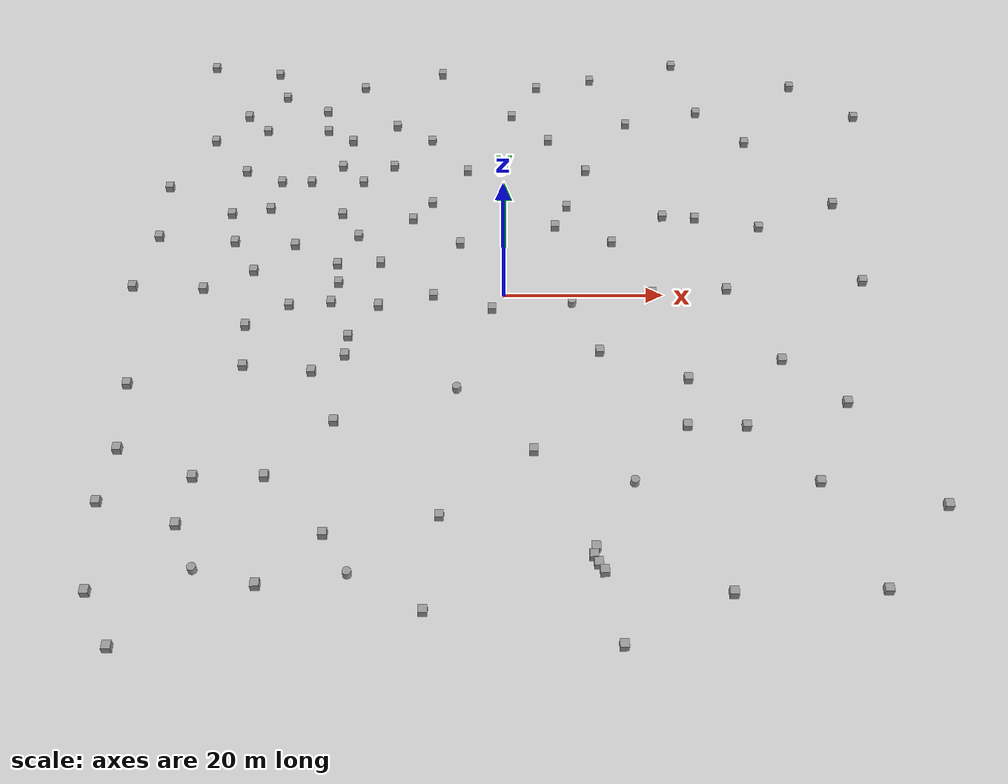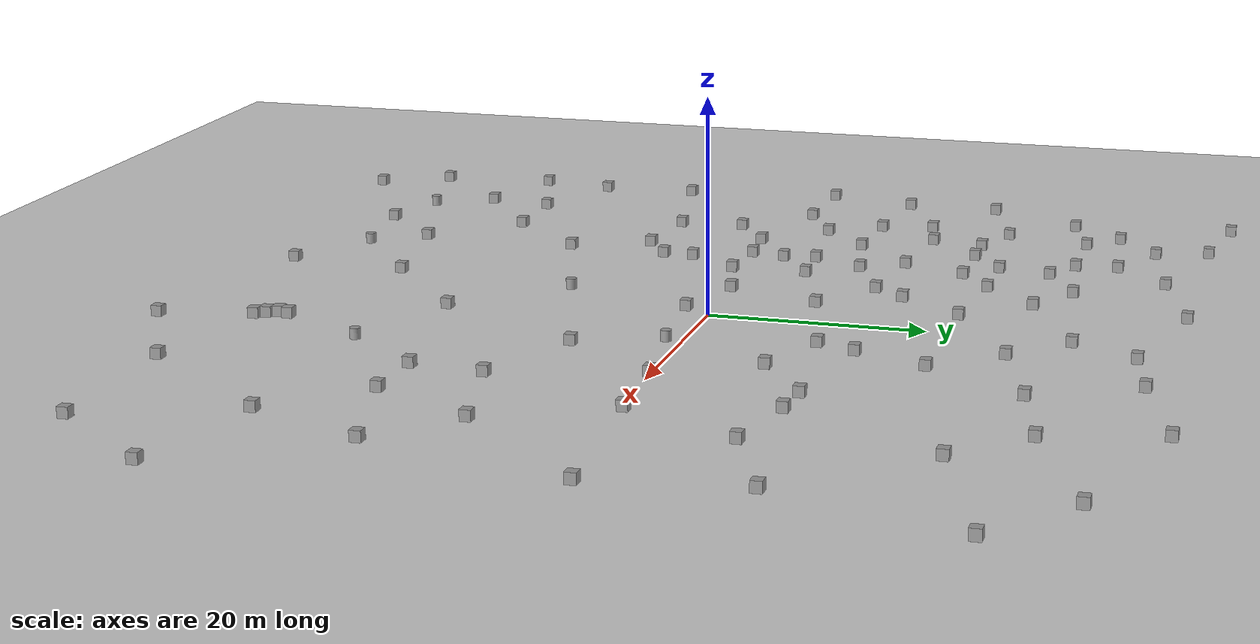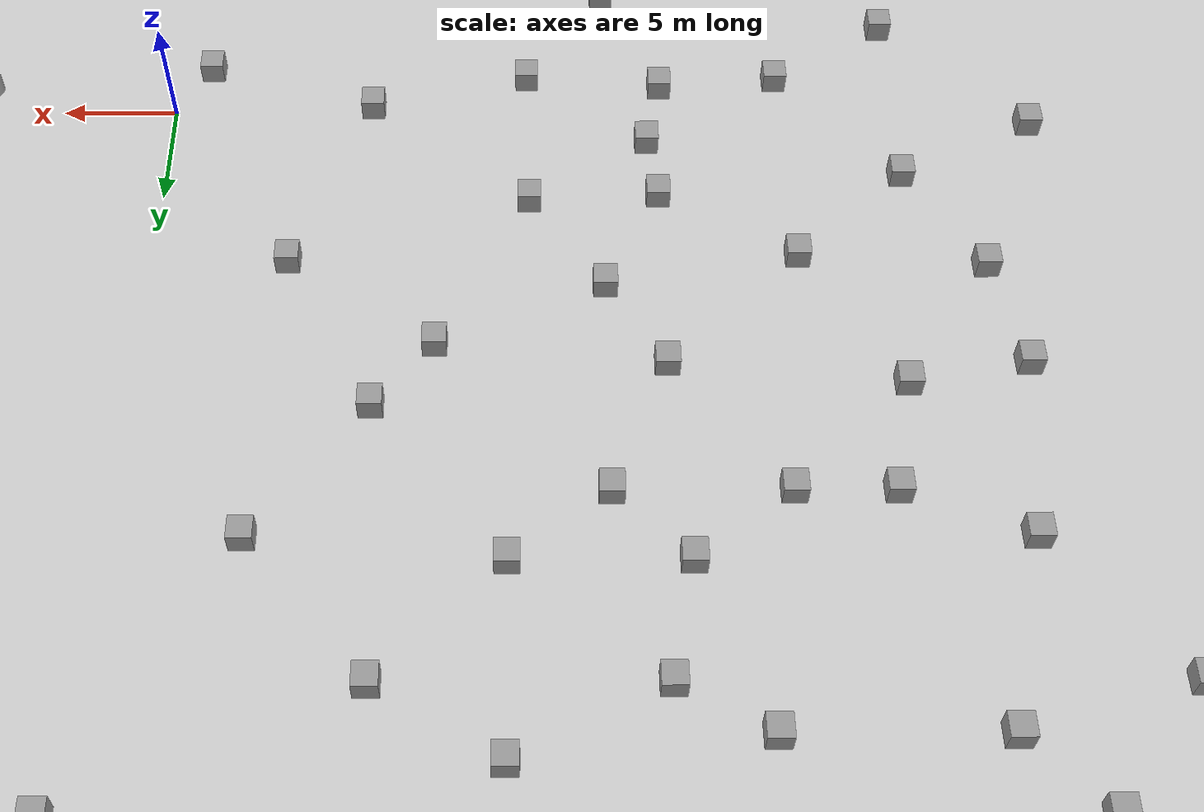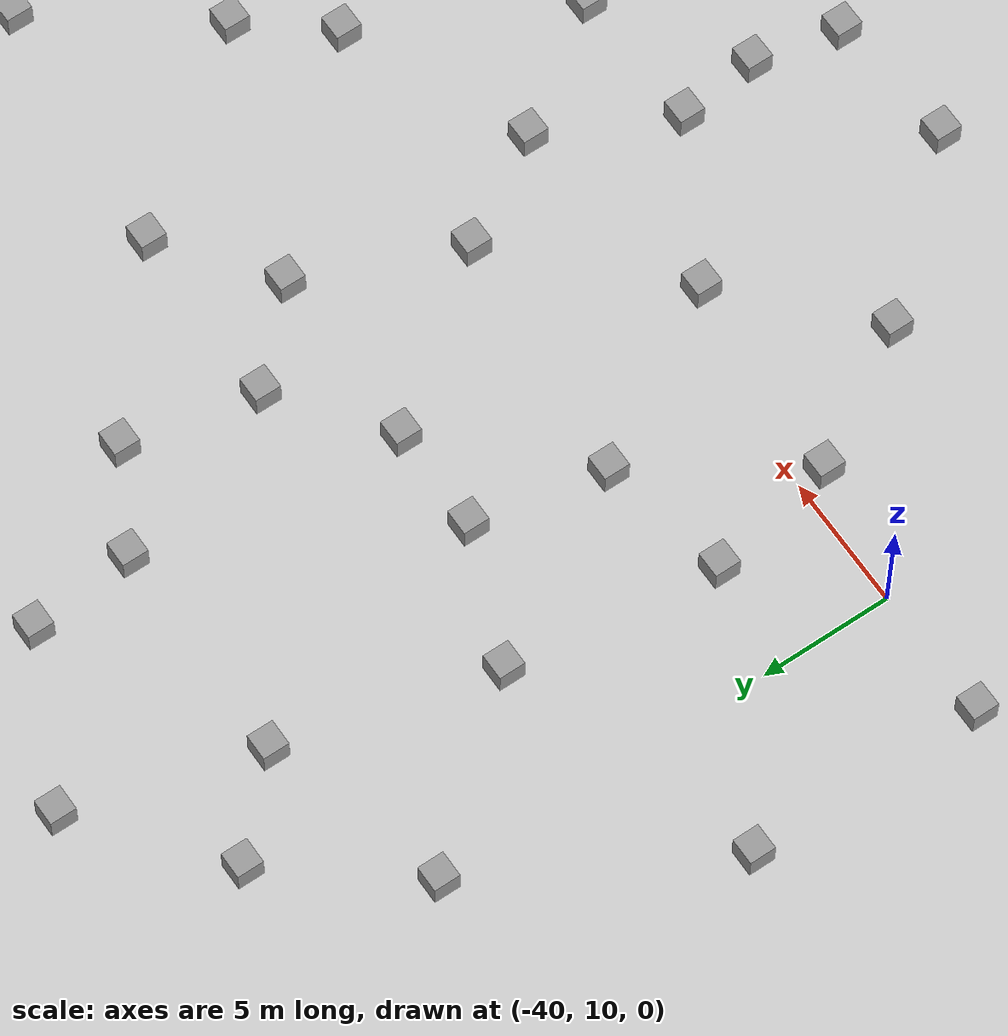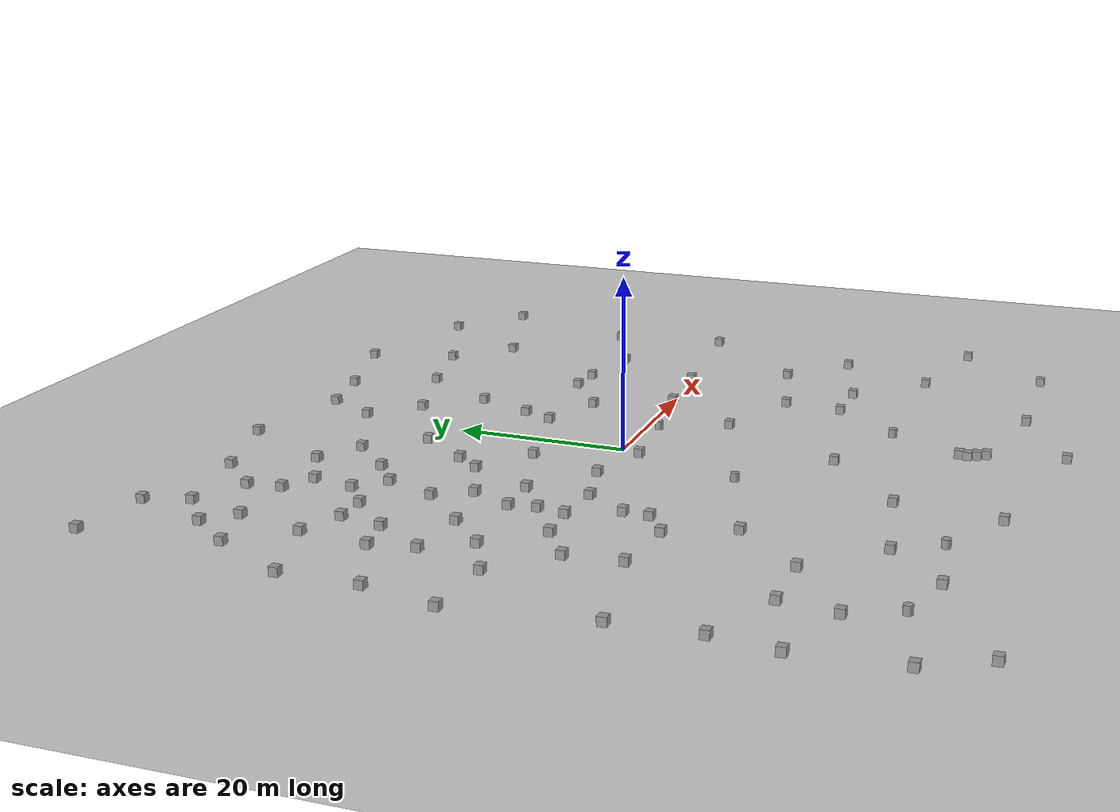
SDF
<sdf version="1.7">
 <world name="default">
  <light name="sun" type="directional">
   <pose>0 0 10 0 -0 0</pose>
   <diffuse>0.8 0.8 0.8 1</diffuse>
   <specular>0.2 0.2 0.2 1</specular>
   <attenuation>
    <range>1000</range>
    <constant>0.9</constant>
    <linear>0.01</linear>
    <quadratic>0.001</quadratic>
   </attenuation>
   <direction>-0.5 0.1 -0.9</direction>
   <spot><inner_angle>0</inner_angle><outer_angle>0</outer_angle><falloff>0</falloff></spot>
  </light>
  <model name="ground_plane">
   <static>1</static>
   <link name="link">
    <collision name="collision">
     <geometry><plane><normal>0 0 1</normal><size>100 100</size></plane></geometry>
     <surface><friction><ode><mu>100</mu><mu2>50</mu2></ode></friction></surface>
    </collision>
    <visual name="visual">
     <cast_shadows>0</cast_shadows>
     <geometry><plane><normal>0 0 1</normal><size>100 100</size></plane></geometry>
     <material>
      <script><uri>file://media/materials/scripts/gazebo.material</uri><name>Gazebo/Grey</name></script>
     </material>
    </visual>
   </link>
  </model>
  <gravity>0 0 -9.8</gravity>
  <magnetic_field>6e-06 2.3e-05 -4.2e-05</magnetic_field>
  <atmosphere type="adiabatic"/>
  <physics type="ode">
   <max_step_size>0.001</max_step_size>
   <real_time_factor>1</real_time_factor>
   <real_time_update_rate>1000</real_time_update_rate>
  </physics>
  <scene><ambient>0.4 0.4 0.4 1</ambient><background>0.7 0.7 0.7 1</background><shadows>1</shadows></scene>
  <spherical_coordinates>
   <surface_model>EARTH_WGS84</surface_model>
   <latitude_deg>0</latitude_deg>
   <longitude_deg>0</longitude_deg>
   <elevation>0</elevation>
   <heading_deg>0</heading_deg>
  </spherical_coordinates>
  <light name="user_directional_light_0" type="directional">
   <pose>-7.86825 7.02908 1 0 -0 0</pose>
   <diffuse>0.5 0.5 0.5 1</diffuse>
   <specular>0.1 0.1 0.1 1</specular>
   <direction>0.1 0.1 -0.9</direction>
   <attenuation>
    <range>20</range>
    <constant>0.5</constant>
    <linear>0.01</linear>
    <quadratic>0.001</quadratic>
   </attenuation>
   <spot><inner_angle>0</inner_angle><outer_angle>0</outer_angle><falloff>0</falloff></spot>
  </light>
  <light name="user_directional_light_1" type="directional">
   <pose>-16.7576 13.165 1 0 -0 0</pose>
   <diffuse>0.5 0.5 0.5 1</diffuse>
   <specular>0.1 0.1 0.1 1</specular>
   <direction>0.1 0.1 -0.9</direction>
   <attenuation>
    <range>20</range>
    <constant>0.5</constant>
    <linear>0.01</linear>
    <quadratic>0.001</quadratic>
   </attenuation>
   <spot><inner_angle>0</inner_angle><outer_angle>0</outer_angle><falloff>0</falloff></spot>
  </light>
  <light name="user_directional_light_2" type="directional">
   <pose>0.944994 13.7599 1 0 -0 0</pose>
   <diffuse>0.5 0.5 0.5 1</diffuse>
   <specular>0.1 0.1 0.1 1</specular>
   <direction>0.1 0.1 -0.9</direction>
   <attenuation>
    <range>20</range>
    <constant>0.5</constant>
    <linear>0.01</linear>
    <quadratic>0.001</quadratic>
   </attenuation>
   <spot><inner_angle>0</inner_angle><outer_angle>0</outer_angle><falloff>0</falloff></spot>
  </light>
  <light name="sun2" type="directional">
   <pose>3.61795 -11.1871 10 0 -0 0</pose>
   <diffuse>0.8 0.8 0.8 1</diffuse>
   <specular>0.2 0.2 0.2 1</specular>
   <attenuation>
    <range>1000</range>
    <constant>0.9</constant>
    <linear>0.01</linear>
    <quadratic>0.001</quadratic>
   </attenuation>
   <direction>-0.5 0.1 -0.9</direction>
   <spot><inner_angle>0</inner_angle><outer_angle>0</outer_angle><falloff>0</falloff></spot>
  </light>
  <model name="unit_box">
   <pose>-1.48602 -2.42929 0.499995 -1e-05 0 0</pose>
   <link name="link">
    <inertial>
     <mass>1</mass>
     <inertia>
      <ixx>0.166667</ixx>
      <ixy>0</ixy>
      <ixz>0</ixz>
      <iyy>0.166667</iyy>
      <iyz>0</iyz>
      <izz>0.166667</izz>
     </inertia>
    </inertial>
    <collision name="collision"><geometry><box><size>1 1 1</size></box></geometry></collision>
    <visual name="visual">
     <geometry><box><size>1 1 1</size></box></geometry>
     <material>
      <script><name>Gazebo/Grey</name><uri>file://media/materials/scripts/gazebo.material</uri></script>
     </material>
    </visual>
   </link>
  </model>
  <model name="unit_box_0">
   <pose>-8.88513 -0.1341 0.499995 0 -1e-05 0</pose>
   <link name="link">
    <inertial>
     <mass>1</mass>
     <inertia>
      <ixx>0.166667</ixx>
      <ixy>0</ixy>
      <ixz>0</ixz>
      <iyy>0.166667</iyy>
      <iyz>0</iyz>
      <izz>0.166667</izz>
     </inertia>
    </inertial>
    <collision name="collision"><geometry><box><size>1 1 1</size></box></geometry></collision>
    <visual name="visual">
     <geometry><box><size>1 1 1</size></box></geometry>
     <material>
      <script><name>Gazebo/Grey</name><uri>file://media/materials/scripts/gazebo.material</uri></script>
     </material>
    </visual>
   </link>
  </model>
  <model name="unit_box_1">
   <pose>-5.71723 8.66868 0.499995 -1e-05 0 0</pose>
   <link name="link">
    <inertial>
     <mass>1</mass>
     <inertia>
      <ixx>0.166667</ixx>
      <ixy>0</ixy>
      <ixz>0</ixz>
      <iyy>0.166667</iyy>
      <iyz>0</iyz>
      <izz>0.166667</izz>
     </inertia>
    </inertial>
    <collision name="collision"><geometry><box><size>1 1 1</size></box></geometry></collision>
    <visual name="visual">
     <geometry><box><size>1 1 1</size></box></geometry>
     <material>
      <script><name>Gazebo/Grey</name><uri>file://media/materials/scripts/gazebo.material</uri></script>
     </material>
    </visual>
   </link>
  </model>
  <model name="unit_box_2">
   <pose>-19.3536 -9.70408 0.499995 0 -1e-05 0</pose>
   <link name="link">
    <inertial>
     <mass>1</mass>
     <inertia>
      <ixx>0.166667</ixx>
      <ixy>0</ixy>
      <ixz>0</ixz>
      <iyy>0.166667</iyy>
      <iyz>0</iyz>
      <izz>0.166667</izz>
     </inertia>
    </inertial>
    <collision name="collision"><geometry><box><size>1 1 1</size></box></geometry></collision>
    <visual name="visual">
     <geometry><box><size>1 1 1</size></box></geometry>
     <material>
      <script><name>Gazebo/Grey</name><uri>file://media/materials/scripts/gazebo.material</uri></script>
     </material>
    </visual>
   </link>
  </model>
  <model name="unit_box_3">
   <pose>-7.15015 -32.3919 0.499995 -1e-05 0 0</pose>
   <link name="link">
    <inertial>
     <mass>1</mass>
     <inertia>
      <ixx>0.166667</ixx>
      <ixy>0</ixy>
      <ixz>0</ixz>
      <iyy>0.166667</iyy>
      <iyz>0</iyz>
      <izz>0.166667</izz>
     </inertia>
    </inertial>
    <collision name="collision"><geometry><box><size>1 1 1</size></box></geometry></collision>
    <visual name="visual">
     <geometry><box><size>1 1 1</size></box></geometry>
     <material>
      <script><name>Gazebo/Grey</name><uri>file://media/materials/scripts/gazebo.material</uri></script>
     </material>
    </visual>
   </link>
  </model>
  <model name="unit_box_4">
   <pose>-19.9233 -19.4512 0.499995 0 -1e-05 0</pose>
   <link name="link">
    <inertial>
     <mass>1</mass>
     <inertia>
      <ixx>0.166667</ixx>
      <ixy>0</ixy>
      <ixz>0</ixz>
      <iyy>0.166667</iyy>
      <iyz>0</iyz>
      <izz>0.166667</izz>
     </inertia>
    </inertial>
    <collision name="collision"><geometry><box><size>1 1 1</size></box></geometry></collision>
    <visual name="visual">
     <geometry><box><size>1 1 1</size></box></geometry>
     <material>
      <script><name>Gazebo/Grey</name><uri>file://media/materials/scripts/gazebo.material</uri></script>
     </material>
    </visual>
   </link>
  </model>
  <model name="unit_box_5">
   <pose>-19.9063 -34.6496 0.499995 -1e-05 0 0</pose>
   <link name="link">
    <inertial>
     <mass>1</mass>
     <inertia>
      <ixx>0.166667</ixx>
      <ixy>0</ixy>
      <ixz>0</ixz>
      <iyy>0.166667</iyy>
      <iyz>0</iyz>
      <izz>0.166667</izz>
     </inertia>
    </inertial>
    <collision name="collision"><geometry><box><size>1 1 1</size></box></geometry></collision>
    <visual name="visual">
     <geometry><box><size>1 1 1</size></box></geometry>
     <material>
      <script><name>Gazebo/Grey</name><uri>file://media/materials/scripts/gazebo.material</uri></script>
     </material>
    </visual>
   </link>
  </model>
  <model name="unit_box_6">
   <pose>-35.2944 -27.2 0.499995 0 -1e-05 0</pose>
   <link name="link">
    <inertial>
     <mass>1</mass>
     <inertia>
      <ixx>0.166667</ixx>
      <ixy>0</ixy>
      <ixz>0</ixz>
      <iyy>0.166667</iyy>
      <iyz>0</iyz>
      <izz>0.166667</izz>
     </inertia>
    </inertial>
    <collision name="collision"><geometry><box><size>1 1 1</size></box></geometry></collision>
    <visual name="visual">
     <geometry><box><size>1 1 1</size></box></geometry>
     <material>
      <script><name>Gazebo/Grey</name><uri>file://media/materials/scripts/gazebo.material</uri></script>
     </material>
    </visual>
   </link>
  </model>
  <model name="unit_box_7">
   <pose>-36.2514 -33.4228 0.499995 -1e-05 0 0</pose>
   <link name="link">
    <inertial>
     <mass>1</mass>
     <inertia>
      <ixx>0.166667</ixx>
      <ixy>0</ixy>
      <ixz>0</ixz>
      <iyy>0.166667</iyy>
      <iyz>0</iyz>
      <izz>0.166667</izz>
     </inertia>
    </inertial>
    <collision name="collision"><geometry><box><size>1 1 1</size></box></geometry></collision>
    <visual name="visual">
     <geometry><box><size>1 1 1</size></box></geometry>
     <material>
      <script><name>Gazebo/Grey</name><uri>file://media/materials/scripts/gazebo.material</uri></script>
     </material>
    </visual>
   </link>
  </model>
  <model name="unit_box_8">
   <pose>-44.5168 -23.3296 0.499995 0 -1e-05 0</pose>
   <link name="link">
    <inertial>
     <mass>1</mass>
     <inertia>
      <ixx>0.166667</ixx>
      <ixy>0</ixy>
      <ixz>0</ixz>
      <iyy>0.166667</iyy>
      <iyz>0</iyz>
      <izz>0.166667</izz>
     </inertia>
    </inertial>
    <collision name="collision"><geometry><box><size>1 1 1</size></box></geometry></collision>
    <visual name="visual">
     <geometry><box><size>1 1 1</size></box></geometry>
     <material>
      <script><name>Gazebo/Grey</name><uri>file://media/materials/scripts/gazebo.material</uri></script>
     </material>
    </visual>
   </link>
  </model>
  <model name="unit_box_9">
   <pose>-45.5805 -30.4463 0.499995 -1e-05 0 0</pose>
   <link name="link">
    <inertial>
     <mass>1</mass>
     <inertia>
      <ixx>0.166667</ixx>
      <ixy>0</ixy>
      <ixz>0</ixz>
      <iyy>0.166667</iyy>
      <iyz>0</iyz>
      <izz>0.166667</izz>
     </inertia>
    </inertial>
    <collision name="collision"><geometry><box><size>1 1 1</size></box></geometry></collision>
    <visual name="visual">
     <geometry><box><size>1 1 1</size></box></geometry>
     <material>
      <script><name>Gazebo/Grey</name><uri>file://media/materials/scripts/gazebo.material</uri></script>
     </material>
    </visual>
   </link>
  </model>
  <model name="unit_box_10">
   <pose>-41.1097 -48.1009 0.499995 0 -1e-05 0</pose>
   <link name="link">
    <inertial>
     <mass>1</mass>
     <inertia>
      <ixx>0.166667</ixx>
      <ixy>0</ixy>
      <ixz>0</ixz>
      <iyy>0.166667</iyy>
      <iyz>0</iyz>
      <izz>0.166667</izz>
     </inertia>
    </inertial>
    <collision name="collision"><geometry><box><size>1 1 1</size></box></geometry></collision>
    <visual name="visual">
     <geometry><box><size>1 1 1</size></box></geometry>
     <material>
      <script><name>Gazebo/Grey</name><uri>file://media/materials/scripts/gazebo.material</uri></script>
     </material>
    </visual>
   </link>
  </model>
  <model name="unit_box_11">
   <pose>-44.6714 -41.6264 0.499995 -1e-05 0 0</pose>
   <link name="link">
    <inertial>
     <mass>1</mass>
     <inertia>
      <ixx>0.166667</ixx>
      <ixy>0</ixy>
      <ixz>0</ixz>
      <iyy>0.166667</iyy>
      <iyz>0</iyz>
      <izz>0.166667</izz>
     </inertia>
    </inertial>
    <collision name="collision"><geometry><box><size>1 1 1</size></box></geometry></collision>
    <visual name="visual">
     <geometry><box><size>1 1 1</size></box></geometry>
     <material>
      <script><name>Gazebo/Grey</name><uri>file://media/materials/scripts/gazebo.material</uri></script>
     </material>
    </visual>
   </link>
  </model>
  <model name="unit_box_12">
   <pose>-26.6021 -40.8845 0.499995 0 -1e-05 0</pose>
   <link name="link">
    <inertial>
     <mass>1</mass>
     <inertia>
      <ixx>0.166667</ixx>
      <ixy>0</ixy>
      <ixz>0</ixz>
      <iyy>0.166667</iyy>
      <iyz>0</iyz>
      <izz>0.166667</izz>
     </inertia>
    </inertial>
    <collision name="collision"><geometry><box><size>1 1 1</size></box></geometry></collision>
    <visual name="visual">
     <geometry><box><size>1 1 1</size></box></geometry>
     <material>
      <script><name>Gazebo/Grey</name><uri>file://media/materials/scripts/gazebo.material</uri></script>
     </material>
    </visual>
   </link>
  </model>
  <model name="unit_box_13">
   <pose>-27.1768 -27.0906 0.499995 -1e-05 0 0</pose>
   <link name="link">
    <inertial>
     <mass>1</mass>
     <inertia>
      <ixx>0.166667</ixx>
      <ixy>0</ixy>
      <ixz>0</ixz>
      <iyy>0.166667</iyy>
      <iyz>0</iyz>
      <izz>0.166667</izz>
     </inertia>
    </inertial>
    <collision name="collision"><geometry><box><size>1 1 1</size></box></geometry></collision>
    <visual name="visual">
     <geometry><box><size>1 1 1</size></box></geometry>
     <material>
      <script><name>Gazebo/Grey</name><uri>file://media/materials/scripts/gazebo.material</uri></script>
     </material>
    </visual>
   </link>
  </model>
  <model name="unit_box_14">
   <pose>-8.52797 -44.0391 0.499995 0 -1e-05 0</pose>
   <link name="link">
    <inertial>
     <mass>1</mass>
     <inertia>
      <ixx>0.166667</ixx>
      <ixy>0</ixy>
      <ixz>0</ixz>
      <iyy>0.166667</iyy>
      <iyz>0</iyz>
      <izz>0.166667</izz>
     </inertia>
    </inertial>
    <collision name="collision"><geometry><box><size>1 1 1</size></box></geometry></collision>
    <visual name="visual">
     <geometry><box><size>1 1 1</size></box></geometry>
     <material>
      <script><name>Gazebo/Grey</name><uri>file://media/materials/scripts/gazebo.material</uri></script>
     </material>
    </visual>
   </link>
  </model>
  <model name="unit_box_15">
   <pose>10.1331 -36.406 0.499995 -1e-05 0 0.002457</pose>
   <link name="link">
    <inertial>
     <mass>1</mass>
     <inertia>
      <ixx>0.166667</ixx>
      <ixy>0</ixy>
      <ixz>0</ixz>
      <iyy>0.166667</iyy>
      <iyz>0</iyz>
      <izz>0.166667</izz>
     </inertia>
    </inertial>
    <collision name="collision"><geometry><box><size>1 1 1</size></box></geometry></collision>
    <visual name="visual">
     <geometry><box><size>1 1 1</size></box></geometry>
     <material>
      <script><name>Gazebo/Grey</name><uri>file://media/materials/scripts/gazebo.material</uri></script>
     </material>
    </visual>
   </link>
  </model>
  <model name="unit_box_16">
   <pose>3.48161 -23.6744 0.499995 0 -1e-05 0</pose>
   <link name="link">
    <inertial>
     <mass>1</mass>
     <inertia>
      <ixx>0.166667</ixx>
      <ixy>0</ixy>
      <ixz>0</ixz>
      <iyy>0.166667</iyy>
      <iyz>0</iyz>
      <izz>0.166667</izz>
     </inertia>
    </inertial>
    <collision name="collision"><geometry><box><size>1 1 1</size></box></geometry></collision>
    <visual name="visual">
     <geometry><box><size>1 1 1</size></box></geometry>
     <material>
      <script><name>Gazebo/Grey</name><uri>file://media/materials/scripts/gazebo.material</uri></script>
     </material>
    </visual>
   </link>
  </model>
  <model name="unit_cylinder">
   <pose>-5.61845 -14.8 0.499993 -3e-06 -1e-06 -0</pose>
   <link name="link">
    <inertial>
     <mass>1</mass>
     <inertia><ixx>0.145833</ixx><ixy>0</ixy><ixz>0</ixz><iyy>0.145833</iyy><iyz>0</iyz><izz>0.125</izz></inertia>
    </inertial>
    <collision name="collision">
     <geometry><cylinder><radius>0.5</radius><length>1</length></cylinder></geometry>
    </collision>
    <visual name="visual">
     <geometry><cylinder><radius>0.5</radius><length>1</length></cylinder></geometry>
     <material>
      <script><name>Gazebo/Grey</name><uri>file://media/materials/scripts/gazebo.material</uri></script>
     </material>
    </visual>
   </link>
  </model>
  <model name="unit_cylinder_0">
   <pose>-16.8552 -39.5664 0.499996 3e-06 1e-06 -0</pose>
   <link name="link">
    <inertial>
     <mass>1</mass>
     <inertia><ixx>0.145833</ixx><ixy>0</ixy><ixz>0</ixz><iyy>0.145833</iyy><iyz>0</iyz><izz>0.125</izz></inertia>
    </inertial>
    <collision name="collision">
     <geometry><cylinder><radius>0.5</radius><length>1</length></cylinder></geometry>
    </collision>
    <visual name="visual">
     <geometry><cylinder><radius>0.5</radius><length>1</length></cylinder></geometry>
     <material>
      <script><name>Gazebo/Grey</name><uri>file://media/materials/scripts/gazebo.material</uri></script>
     </material>
    </visual>
   </link>
  </model>
  <model name="unit_cylinder_1">
   <pose>14.8613 -27.982 0.499996 3e-06 1e-06 -0</pose>
   <link name="link">
    <inertial>
     <mass>1</mass>
     <inertia><ixx>0.145833</ixx><ixy>0</ixy><ixz>0</ixz><iyy>0.145833</iyy><iyz>0</iyz><izz>0.125</izz></inertia>
    </inertial>
    <collision name="collision">
     <geometry><cylinder><radius>0.5</radius><length>1</length></cylinder></geometry>
    </collision>
    <visual name="visual">
     <geometry><cylinder><radius>0.5</radius><length>1</length></cylinder></geometry>
     <material>
      <script><name>Gazebo/Grey</name><uri>file://media/materials/scripts/gazebo.material</uri></script>
     </material>
    </visual>
   </link>
  </model>
  <model name="unit_box_17">
   <pose>12.6077 -48.0211 0.499995 0 -1e-05 0</pose>
   <link name="link">
    <inertial>
     <mass>1</mass>
     <inertia>
      <ixx>0.166667</ixx>
      <ixy>0</ixy>
      <ixz>0</ixz>
      <iyy>0.166667</iyy>
      <iyz>0</iyz>
      <izz>0.166667</izz>
     </inertia>
    </inertial>
    <collision name="collision"><geometry><box><size>1 1 1</size></box></geometry></collision>
    <visual name="visual">
     <geometry><box><size>1 1 1</size></box></geometry>
     <material>
      <script><name>Gazebo/Grey</name><uri>file://media/materials/scripts/gazebo.material</uri></script>
     </material>
    </visual>
   </link>
  </model>
  <model name="unit_box_18">
   <pose>9.88946 -37.4067 0.5 0 -0 0.002476</pose>
   <link name="link">
    <inertial>
     <mass>1</mass>
     <inertia>
      <ixx>0.166667</ixx>
      <ixy>0</ixy>
      <ixz>0</ixz>
      <iyy>0.166667</iyy>
      <iyz>0</iyz>
      <izz>0.166667</izz>
     </inertia>
    </inertial>
    <collision name="collision"><geometry><box><size>1 1 1</size></box></geometry></collision>
    <visual name="visual">
     <geometry><box><size>1 1 1</size></box></geometry>
     <material>
      <script><name>Gazebo/Grey</name><uri>file://media/materials/scripts/gazebo.material</uri></script>
     </material>
    </visual>
   </link>
  </model>
  <model name="unit_box_19">
   <pose>10.3433 -38.409 0.499995 0 1e-05 0.058143</pose>
   <link name="link">
    <inertial>
     <mass>1</mass>
     <inertia>
      <ixx>0.166667</ixx>
      <ixy>0</ixy>
      <ixz>0</ixz>
      <iyy>0.166667</iyy>
      <iyz>0</iyz>
      <izz>0.166667</izz>
     </inertia>
    </inertial>
    <collision name="collision"><geometry><box><size>1 1 1</size></box></geometry></collision>
    <visual name="visual">
     <geometry><box><size>1 1 1</size></box></geometry>
     <material>
      <script><name>Gazebo/Grey</name><uri>file://media/materials/scripts/gazebo.material</uri></script>
     </material>
    </visual>
   </link>
  </model>
  <model name="unit_box_20">
   <pose>10.9517 -39.3753 0.5 0 -0 0.058332</pose>
   <link name="link">
    <inertial>
     <mass>1</mass>
     <inertia>
      <ixx>0.166667</ixx>
      <ixy>0</ixy>
      <ixz>0</ixz>
      <iyy>0.166667</iyy>
      <iyz>0</iyz>
      <izz>0.166667</izz>
     </inertia>
    </inertial>
    <collision name="collision"><geometry><box><size>1 1 1</size></box></geometry></collision>
    <visual name="visual">
     <geometry><box><size>1 1 1</size></box></geometry>
     <material>
      <script><name>Gazebo/Grey</name><uri>file://media/materials/scripts/gazebo.material</uri></script>
     </material>
    </visual>
   </link>
  </model>
  <model name="unit_cylinder_2">
   <pose>8.4882 -1.47924 0.499993 -4e-06 -2e-06 -0</pose>
   <link name="link">
    <inertial>
     <mass>1</mass>
     <inertia><ixx>0.145833</ixx><ixy>0</ixy><ixz>0</ixz><iyy>0.145833</iyy><iyz>0</iyz><izz>0.125</izz></inertia>
    </inertial>
    <collision name="collision">
     <geometry><cylinder><radius>0.5</radius><length>1</length></cylinder></geometry>
    </collision>
    <visual name="visual">
     <geometry><cylinder><radius>0.5</radius><length>1</length></cylinder></geometry>
     <material>
      <script><name>Gazebo/Grey</name><uri>file://media/materials/scripts/gazebo.material</uri></script>
     </material>
    </visual>
   </link>
  </model>
  <model name="unit_cylinder_3">
   <pose>-33.6244 -38.9876 0.499993 -4e-06 -2e-06 -0</pose>
   <link name="link">
    <inertial>
     <mass>1</mass>
     <inertia><ixx>0.145833</ixx><ixy>0</ixy><ixz>0</ixz><iyy>0.145833</iyy><iyz>0</iyz><izz>0.125</izz></inertia>
    </inertial>
    <collision name="collision">
     <geometry><cylinder><radius>0.5</radius><length>1</length></cylinder></geometry>
    </collision>
    <visual name="visual">
     <geometry><cylinder><radius>0.5</radius><length>1</length></cylinder></geometry>
     <material>
      <script><name>Gazebo/Grey</name><uri>file://media/materials/scripts/gazebo.material</uri></script>
     </material>
    </visual>
   </link>
  </model>
  <model name="unit_box_21">
   <pose>-15.7321 -1.82075 0.499995 0 -1e-05 0</pose>
   <link name="link">
    <inertial>
     <mass>1</mass>
     <inertia>
      <ixx>0.166667</ixx>
      <ixy>0</ixy>
      <ixz>0</ixz>
      <iyy>0.166667</iyy>
      <iyz>0</iyz>
      <izz>0.166667</izz>
     </inertia>
    </inertial>
    <collision name="collision"><geometry><box><size>1 1 1</size></box></geometry></collision>
    <visual name="visual">
     <geometry><box><size>1 1 1</size></box></geometry>
     <material>
      <script><name>Gazebo/Grey</name><uri>file://media/materials/scripts/gazebo.material</uri></script>
     </material>
    </visual>
   </link>
  </model>
  <model name="unit_box_22">
   <pose>11.6432 -9.19401 0.499995 -1e-05 0 0</pose>
   <link name="link">
    <inertial>
     <mass>1</mass>
     <inertia>
      <ixx>0.166667</ixx>
      <ixy>0</ixy>
      <ixz>0</ixz>
      <iyy>0.166667</iyy>
      <iyz>0</iyz>
      <izz>0.166667</izz>
     </inertia>
    </inertial>
    <collision name="collision"><geometry><box><size>1 1 1</size></box></geometry></collision>
    <visual name="visual">
     <geometry><box><size>1 1 1</size></box></geometry>
     <material>
      <script><name>Gazebo/Grey</name><uri>file://media/materials/scripts/gazebo.material</uri></script>
     </material>
    </visual>
   </link>
  </model>
  <model name="unit_box_23">
   <pose>22.1082 -13.3925 0.499995 0 -1e-05 0</pose>
   <link name="link">
    <inertial>
     <mass>1</mass>
     <inertia>
      <ixx>0.166667</ixx>
      <ixy>0</ixy>
      <ixz>0</ixz>
      <iyy>0.166667</iyy>
      <iyz>0</iyz>
      <izz>0.166667</izz>
     </inertia>
    </inertial>
    <collision name="collision"><geometry><box><size>1 1 1</size></box></geometry></collision>
    <visual name="visual">
     <geometry><box><size>1 1 1</size></box></geometry>
     <material>
      <script><name>Gazebo/Grey</name><uri>file://media/materials/scripts/gazebo.material</uri></script>
     </material>
    </visual>
   </link>
  </model>
  <model name="unit_box_24">
   <pose>28.3535 -20.338 0.499995 -1e-05 0 0</pose>
   <link name="link">
    <inertial>
     <mass>1</mass>
     <inertia>
      <ixx>0.166667</ixx>
      <ixy>0</ixy>
      <ixz>0</ixz>
      <iyy>0.166667</iyy>
      <iyz>0</iyz>
      <izz>0.166667</izz>
     </inertia>
    </inertial>
    <collision name="collision"><geometry><box><size>1 1 1</size></box></geometry></collision>
    <visual name="visual">
     <geometry><box><size>1 1 1</size></box></geometry>
     <material>
      <script><name>Gazebo/Grey</name><uri>file://media/materials/scripts/gazebo.material</uri></script>
     </material>
    </visual>
   </link>
  </model>
  <model name="unit_box_25">
   <pose>21.4438 -20.2791 0.499995 0 -1e-05 0</pose>
   <link name="link">
    <inertial>
     <mass>1</mass>
     <inertia>
      <ixx>0.166667</ixx>
      <ixy>0</ixy>
      <ixz>0</ixz>
      <iyy>0.166667</iyy>
      <iyz>0</iyz>
      <izz>0.166667</izz>
     </inertia>
    </inertial>
    <collision name="collision"><geometry><box><size>1 1 1</size></box></geometry></collision>
    <visual name="visual">
     <geometry><box><size>1 1 1</size></box></geometry>
     <material>
      <script><name>Gazebo/Grey</name><uri>file://media/materials/scripts/gazebo.material</uri></script>
     </material>
    </visual>
   </link>
  </model>
  <model name="unit_box_26">
   <pose>49.7253 -31.1907 0.499995 -1e-05 0 0</pose>
   <link name="link">
    <inertial>
     <mass>1</mass>
     <inertia>
      <ixx>0.166667</ixx>
      <ixy>0</ixy>
      <ixz>0</ixz>
      <iyy>0.166667</iyy>
      <iyz>0</iyz>
      <izz>0.166667</izz>
     </inertia>
    </inertial>
    <collision name="collision"><geometry><box><size>1 1 1</size></box></geometry></collision>
    <visual name="visual">
     <geometry><box><size>1 1 1</size></box></geometry>
     <material>
      <script><name>Gazebo/Grey</name><uri>file://media/materials/scripts/gazebo.material</uri></script>
     </material>
    </visual>
   </link>
  </model>
  <model name="unit_box_27">
   <pose>41.1975 -41.661 0.499995 0 -1e-05 0</pose>
   <link name="link">
    <inertial>
     <mass>1</mass>
     <inertia>
      <ixx>0.166667</ixx>
      <ixy>0</ixy>
      <ixz>0</ixz>
      <iyy>0.166667</iyy>
      <iyz>0</iyz>
      <izz>0.166667</izz>
     </inertia>
    </inertial>
    <collision name="collision"><geometry><box><size>1 1 1</size></box></geometry></collision>
    <visual name="visual">
     <geometry><box><size>1 1 1</size></box></geometry>
     <material>
      <script><name>Gazebo/Grey</name><uri>file://media/materials/scripts/gazebo.material</uri></script>
     </material>
    </visual>
   </link>
  </model>
  <model name="unit_box_28">
   <pose>24.6321 -41.9984 0.499995 -1e-05 0 0</pose>
   <link name="link">
    <inertial>
     <mass>1</mass>
     <inertia>
      <ixx>0.166667</ixx>
      <ixy>0</ixy>
      <ixz>0</ixz>
      <iyy>0.166667</iyy>
      <iyz>0</iyz>
      <izz>0.166667</izz>
     </inertia>
    </inertial>
    <collision name="collision"><geometry><box><size>1 1 1</size></box></geometry></collision>
    <visual name="visual">
     <geometry><box><size>1 1 1</size></box></geometry>
     <material>
      <script><name>Gazebo/Grey</name><uri>file://media/materials/scripts/gazebo.material</uri></script>
     </material>
    </visual>
   </link>
  </model>
  <model name="unit_box_29">
   <pose>35.8618 -28.0283 0.499995 0 -1e-05 0</pose>
   <link name="link">
    <inertial>
     <mass>1</mass>
     <inertia>
      <ixx>0.166667</ixx>
      <ixy>0</ixy>
      <ixz>0</ixz>
      <iyy>0.166667</iyy>
      <iyz>0</iyz>
      <izz>0.166667</izz>
     </inertia>
    </inertial>
    <collision name="collision"><geometry><box><size>1 1 1</size></box></geometry></collision>
    <visual name="visual">
     <geometry><box><size>1 1 1</size></box></geometry>
     <material>
      <script><name>Gazebo/Grey</name><uri>file://media/materials/scripts/gazebo.material</uri></script>
     </material>
    </visual>
   </link>
  </model>
  <model name="unit_box_30">
   <pose>40.6173 -17.0084 0.499995 -1e-05 0 0</pose>
   <link name="link">
    <inertial>
     <mass>1</mass>
     <inertia>
      <ixx>0.166667</ixx>
      <ixy>0</ixy>
      <ixz>0</ixz>
      <iyy>0.166667</iyy>
      <iyz>0</iyz>
      <izz>0.166667</izz>
     </inertia>
    </inertial>
    <collision name="collision"><geometry><box><size>1 1 1</size></box></geometry></collision>
    <visual name="visual">
     <geometry><box><size>1 1 1</size></box></geometry>
     <material>
      <script><name>Gazebo/Grey</name><uri>file://media/materials/scripts/gazebo.material</uri></script>
     </material>
    </visual>
   </link>
  </model>
  <model name="unit_box_31">
   <pose>33.649 -10.5946 0.499995 0 -1e-05 0</pose>
   <link name="link">
    <inertial>
     <mass>1</mass>
     <inertia>
      <ixx>0.166667</ixx>
      <ixy>0</ixy>
      <ixz>0</ixz>
      <iyy>0.166667</iyy>
      <iyz>0</iyz>
      <izz>0.166667</izz>
     </inertia>
    </inertial>
    <collision name="collision"><geometry><box><size>1 1 1</size></box></geometry></collision>
    <visual name="visual">
     <geometry><box><size>1 1 1</size></box></geometry>
     <material>
      <script><name>Gazebo/Grey</name><uri>file://media/materials/scripts/gazebo.material</uri></script>
     </material>
    </visual>
   </link>
  </model>
  <model name="unit_box_32">
   <pose>28.054 0.63763 0.499995 -1e-05 0 0</pose>
   <link name="link">
    <inertial>
     <mass>1</mass>
     <inertia>
      <ixx>0.166667</ixx>
      <ixy>0</ixy>
      <ixz>0</ixz>
      <iyy>0.166667</iyy>
      <iyz>0</iyz>
      <izz>0.166667</izz>
     </inertia>
    </inertial>
    <collision name="collision"><geometry><box><size>1 1 1</size></box></geometry></collision>
    <visual name="visual">
     <geometry><box><size>1 1 1</size></box></geometry>
     <material>
      <script><name>Gazebo/Grey</name><uri>file://media/materials/scripts/gazebo.material</uri></script>
     </material>
    </visual>
   </link>
  </model>
  <model name="unit_box_33">
   <pose>18.6243 0.062599 0.499995 0 -1e-05 0</pose>
   <link name="link">
    <inertial>
     <mass>1</mass>
     <inertia>
      <ixx>0.166667</ixx>
      <ixy>0</ixy>
      <ixz>0</ixz>
      <iyy>0.166667</iyy>
      <iyz>0</iyz>
      <izz>0.166667</izz>
     </inertia>
    </inertial>
    <collision name="collision"><geometry><box><size>1 1 1</size></box></geometry></collision>
    <visual name="visual">
     <geometry><box><size>1 1 1</size></box></geometry>
     <material>
      <script><name>Gazebo/Grey</name><uri>file://media/materials/scripts/gazebo.material</uri></script>
     </material>
    </visual>
   </link>
  </model>
  <model name="unit_box_34">
   <pose>20.8407 13.4227 0.499995 -1e-05 0 0</pose>
   <link name="link">
    <inertial>
     <mass>1</mass>
     <inertia>
      <ixx>0.166667</ixx>
      <ixy>0</ixy>
      <ixz>0</ixz>
      <iyy>0.166667</iyy>
      <iyz>0</iyz>
      <izz>0.166667</izz>
     </inertia>
    </inertial>
    <collision name="collision"><geometry><box><size>1 1 1</size></box></geometry></collision>
    <visual name="visual">
     <geometry><box><size>1 1 1</size></box></geometry>
     <material>
      <script><name>Gazebo/Grey</name><uri>file://media/materials/scripts/gazebo.material</uri></script>
     </material>
    </visual>
   </link>
  </model>
  <model name="unit_box_35">
   <pose>8.23612 15.2996 0.499995 0 -1e-05 0</pose>
   <link name="link">
    <inertial>
     <mass>1</mass>
     <inertia>
      <ixx>0.166667</ixx>
      <ixy>0</ixy>
      <ixz>0</ixz>
      <iyy>0.166667</iyy>
      <iyz>0</iyz>
      <izz>0.166667</izz>
     </inertia>
    </inertial>
    <collision name="collision"><geometry><box><size>1 1 1</size></box></geometry></collision>
    <visual name="visual">
     <geometry><box><size>1 1 1</size></box></geometry>
     <material>
      <script><name>Gazebo/Grey</name><uri>file://media/materials/scripts/gazebo.material</uri></script>
     </material>
    </visual>
   </link>
  </model>
  <model name="unit_box_36">
   <pose>33.3487 11.4202 0.499995 -1e-05 0 0</pose>
   <link name="link">
    <inertial>
     <mass>1</mass>
     <inertia>
      <ixx>0.166667</ixx>
      <ixy>0</ixy>
      <ixz>0</ixz>
      <iyy>0.166667</iyy>
      <iyz>0</iyz>
      <izz>0.166667</izz>
     </inertia>
    </inertial>
    <collision name="collision"><geometry><box><size>1 1 1</size></box></geometry></collision>
    <visual name="visual">
     <geometry><box><size>1 1 1</size></box></geometry>
     <material>
      <script><name>Gazebo/Grey</name><uri>file://media/materials/scripts/gazebo.material</uri></script>
     </material>
    </visual>
   </link>
  </model>
  <model name="unit_box_37">
   <pose>25.0798 13.0718 0.499995 0 -1e-05 0</pose>
   <link name="link">
    <inertial>
     <mass>1</mass>
     <inertia>
      <ixx>0.166667</ixx>
      <ixy>0</ixy>
      <ixz>0</ixz>
      <iyy>0.166667</iyy>
      <iyz>0</iyz>
      <izz>0.166667</izz>
     </inertia>
    </inertial>
    <collision name="collision"><geometry><box><size>1 1 1</size></box></geometry></collision>
    <visual name="visual">
     <geometry><box><size>1 1 1</size></box></geometry>
     <material>
      <script><name>Gazebo/Grey</name><uri>file://media/materials/scripts/gazebo.material</uri></script>
     </material>
    </visual>
   </link>
  </model>
  <model name="unit_box_38">
   <pose>13.9466 8.80757 0.499995 -1e-05 0 0</pose>
   <link name="link">
    <inertial>
     <mass>1</mass>
     <inertia>
      <ixx>0.166667</ixx>
      <ixy>0</ixy>
      <ixz>0</ixz>
      <iyy>0.166667</iyy>
      <iyz>0</iyz>
      <izz>0.166667</izz>
     </inertia>
    </inertial>
    <collision name="collision"><geometry><box><size>1 1 1</size></box></geometry></collision>
    <visual name="visual">
     <geometry><box><size>1 1 1</size></box></geometry>
     <material>
      <script><name>Gazebo/Grey</name><uri>file://media/materials/scripts/gazebo.material</uri></script>
     </material>
    </visual>
   </link>
  </model>
  <model name="unit_box_39">
   <pose>6.6357 11.6617 0.499995 0 -1e-05 0</pose>
   <link name="link">
    <inertial>
     <mass>1</mass>
     <inertia>
      <ixx>0.166667</ixx>
      <ixy>0</ixy>
      <ixz>0</ixz>
      <iyy>0.166667</iyy>
      <iyz>0</iyz>
      <izz>0.166667</izz>
     </inertia>
    </inertial>
    <collision name="collision"><geometry><box><size>1 1 1</size></box></geometry></collision>
    <visual name="visual">
     <geometry><box><size>1 1 1</size></box></geometry>
     <material>
      <script><name>Gazebo/Grey</name><uri>file://media/materials/scripts/gazebo.material</uri></script>
     </material>
    </visual>
   </link>
  </model>
  <model name="unit_box_40">
   <pose>43.6808 15.664 0.499995 -1e-05 0 0</pose>
   <link name="link">
    <inertial>
     <mass>1</mass>
     <inertia>
      <ixx>0.166667</ixx>
      <ixy>0</ixy>
      <ixz>0</ixz>
      <iyy>0.166667</iyy>
      <iyz>0</iyz>
      <izz>0.166667</izz>
     </inertia>
    </inertial>
    <collision name="collision"><geometry><box><size>1 1 1</size></box></geometry></collision>
    <visual name="visual">
     <geometry><box><size>1 1 1</size></box></geometry>
     <material>
      <script><name>Gazebo/Grey</name><uri>file://media/materials/scripts/gazebo.material</uri></script>
     </material>
    </visual>
   </link>
  </model>
  <model name="unit_box_41">
   <pose>45.4584 2.03539 0.499995 0 -1e-05 0</pose>
   <link name="link">
    <inertial>
     <mass>1</mass>
     <inertia>
      <ixx>0.166667</ixx>
      <ixy>0</ixy>
      <ixz>0</ixz>
      <iyy>0.166667</iyy>
      <iyz>0</iyz>
      <izz>0.166667</izz>
     </inertia>
    </inertial>
    <collision name="collision"><geometry><box><size>1 1 1</size></box></geometry></collision>
    <visual name="visual">
     <geometry><box><size>1 1 1</size></box></geometry>
     <material>
      <script><name>Gazebo/Grey</name><uri>file://media/materials/scripts/gazebo.material</uri></script>
     </material>
    </visual>
   </link>
  </model>
  <model name="unit_box_42">
   <pose>40.8949 39.0969 0.499995 -1e-05 0 0</pose>
   <link name="link">
    <inertial>
     <mass>1</mass>
     <inertia>
      <ixx>0.166667</ixx>
      <ixy>0</ixy>
      <ixz>0</ixz>
      <iyy>0.166667</iyy>
      <iyz>0</iyz>
      <izz>0.166667</izz>
     </inertia>
    </inertial>
    <collision name="collision"><geometry><box><size>1 1 1</size></box></geometry></collision>
    <visual name="visual">
     <geometry><box><size>1 1 1</size></box></geometry>
     <material>
      <script><name>Gazebo/Grey</name><uri>file://media/materials/scripts/gazebo.material</uri></script>
     </material>
    </visual>
   </link>
  </model>
  <model name="unit_box_43">
   <pose>49.1341 32.6758 0.499995 0 -1e-05 0</pose>
   <link name="link">
    <inertial>
     <mass>1</mass>
     <inertia>
      <ixx>0.166667</ixx>
      <ixy>0</ixy>
      <ixz>0</ixz>
      <iyy>0.166667</iyy>
      <iyz>0</iyz>
      <izz>0.166667</izz>
     </inertia>
    </inertial>
    <collision name="collision"><geometry><box><size>1 1 1</size></box></geometry></collision>
    <visual name="visual">
     <geometry><box><size>1 1 1</size></box></geometry>
     <material>
      <script><name>Gazebo/Grey</name><uri>file://media/materials/scripts/gazebo.material</uri></script>
     </material>
    </visual>
   </link>
  </model>
  <model name="unit_box_44">
   <pose>33.1702 27.5087 0.499995 -1e-05 0 0</pose>
   <link name="link">
    <inertial>
     <mass>1</mass>
     <inertia>
      <ixx>0.166667</ixx>
      <ixy>0</ixy>
      <ixz>0</ixz>
      <iyy>0.166667</iyy>
      <iyz>0</iyz>
      <izz>0.166667</izz>
     </inertia>
    </inertial>
    <collision name="collision"><geometry><box><size>1 1 1</size></box></geometry></collision>
    <visual name="visual">
     <geometry><box><size>1 1 1</size></box></geometry>
     <material>
      <script><name>Gazebo/Grey</name><uri>file://media/materials/scripts/gazebo.material</uri></script>
     </material>
    </visual>
   </link>
  </model>
  <model name="unit_box_45">
   <pose>24.2351 43.7886 0.499995 0 -1e-05 0</pose>
   <link name="link">
    <inertial>
     <mass>1</mass>
     <inertia>
      <ixx>0.166667</ixx>
      <ixy>0</ixy>
      <ixz>0</ixz>
      <iyy>0.166667</iyy>
      <iyz>0</iyz>
      <izz>0.166667</izz>
     </inertia>
    </inertial>
    <collision name="collision"><geometry><box><size>1 1 1</size></box></geometry></collision>
    <visual name="visual">
     <geometry><box><size>1 1 1</size></box></geometry>
     <material>
      <script><name>Gazebo/Grey</name><uri>file://media/materials/scripts/gazebo.material</uri></script>
     </material>
    </visual>
   </link>
  </model>
  <model name="unit_box_46">
   <pose>26.9566 33.5682 0.499995 -1e-05 0 0</pose>
   <link name="link">
    <inertial>
     <mass>1</mass>
     <inertia>
      <ixx>0.166667</ixx>
      <ixy>0</ixy>
      <ixz>0</ixz>
      <iyy>0.166667</iyy>
      <iyz>0</iyz>
      <izz>0.166667</izz>
     </inertia>
    </inertial>
    <collision name="collision"><geometry><box><size>1 1 1</size></box></geometry></collision>
    <visual name="visual">
     <geometry><box><size>1 1 1</size></box></geometry>
     <material>
      <script><name>Gazebo/Grey</name><uri>file://media/materials/scripts/gazebo.material</uri></script>
     </material>
    </visual>
   </link>
  </model>
  <model name="unit_box_47">
   <pose>16.9011 31.2196 0.499995 0 -1e-05 0</pose>
   <link name="link">
    <inertial>
     <mass>1</mass>
     <inertia>
      <ixx>0.166667</ixx>
      <ixy>0</ixy>
      <ixz>0</ixz>
      <iyy>0.166667</iyy>
      <iyz>0</iyz>
      <izz>0.166667</izz>
     </inertia>
    </inertial>
    <collision name="collision"><geometry><box><size>1 1 1</size></box></geometry></collision>
    <visual name="visual">
     <geometry><box><size>1 1 1</size></box></geometry>
     <material>
      <script><name>Gazebo/Grey</name><uri>file://media/materials/scripts/gazebo.material</uri></script>
     </material>
    </visual>
   </link>
  </model>
  <model name="unit_box_47_clone">
   <pose>12.209 40.5091 0.499995 -1e-05 -0 0</pose>
   <link name="link">
    <inertial>
     <mass>1</mass>
     <inertia>
      <ixx>0.166667</ixx>
      <ixy>0</ixy>
      <ixz>0</ixz>
      <iyy>0.166667</iyy>
      <iyz>0</iyz>
      <izz>0.166667</izz>
     </inertia>
    </inertial>
    <collision name="collision"><geometry><box><size>1 1 1</size></box></geometry></collision>
    <visual name="visual">
     <geometry><box><size>1 1 1</size></box></geometry>
     <material>
      <script><name>Gazebo/Grey</name><uri>file://media/materials/scripts/gazebo.material</uri></script>
     </material>
    </visual>
   </link>
  </model>
  <model name="unit_box_47_clone_0">
   <pose>11 22 0.499995 0 -1e-05 0</pose>
   <link name="link">
    <inertial>
     <mass>1</mass>
     <inertia>
      <ixx>0.166667</ixx>
      <ixy>0</ixy>
      <ixz>0</ixz>
      <iyy>0.166667</iyy>
      <iyz>0</iyz>
      <izz>0.166667</izz>
     </inertia>
    </inertial>
    <collision name="collision"><geometry><box><size>1 1 1</size></box></geometry></collision>
    <visual name="visual">
     <geometry><box><size>1 1 1</size></box></geometry>
     <material>
      <script><name>Gazebo/Grey</name><uri>file://media/materials/scripts/gazebo.material</uri></script>
     </material>
    </visual>
   </link>
  </model>
  <model name="unit_box_47_clone_1">
   <pose>6 28 0.499995 -1e-05 0 0</pose>
   <link name="link">
    <inertial>
     <mass>1</mass>
     <inertia>
      <ixx>0.166667</ixx>
      <ixy>0</ixy>
      <ixz>0</ixz>
      <iyy>0.166667</iyy>
      <iyz>0</iyz>
      <izz>0.166667</izz>
     </inertia>
    </inertial>
    <collision name="collision"><geometry><box><size>1 1 1</size></box></geometry></collision>
    <visual name="visual">
     <geometry><box><size>1 1 1</size></box></geometry>
     <material>
      <script><name>Gazebo/Grey</name><uri>file://media/materials/scripts/gazebo.material</uri></script>
     </material>
    </visual>
   </link>
  </model>
  <model name="unit_box_47_clone_2">
   <pose>4.50003 39 0.499995 0 -1e-05 0</pose>
   <link name="link">
    <inertial>
     <mass>1</mass>
     <inertia>
      <ixx>0.166667</ixx>
      <ixy>0</ixy>
      <ixz>0</ixz>
      <iyy>0.166667</iyy>
      <iyz>0</iyz>
      <izz>0.166667</izz>
     </inertia>
    </inertial>
    <collision name="collision"><geometry><box><size>1 1 1</size></box></geometry></collision>
    <visual name="visual">
     <geometry><box><size>1 1 1</size></box></geometry>
     <material>
      <script><name>Gazebo/Grey</name><uri>file://media/materials/scripts/gazebo.material</uri></script>
     </material>
    </visual>
   </link>
  </model>
  <model name="unit_box_47_clone_3">
   <pose>0.999995 33 0.499995 0 -1e-05 0</pose>
   <link name="link">
    <inertial>
     <mass>1</mass>
     <inertia>
      <ixx>0.166667</ixx>
      <ixy>0</ixy>
      <ixz>0</ixz>
      <iyy>0.166667</iyy>
      <iyz>0</iyz>
      <izz>0.166667</izz>
     </inertia>
    </inertial>
    <collision name="collision"><geometry><box><size>1 1 1</size></box></geometry></collision>
    <visual name="visual">
     <geometry><box><size>1 1 1</size></box></geometry>
     <material>
      <script><name>Gazebo/Grey</name><uri>file://media/materials/scripts/gazebo.material</uri></script>
     </material>
    </visual>
   </link>
  </model>
  <model name="unit_box_47_clone_4">
   <pose>-5 22 0.499995 -1e-05 0 0</pose>
   <link name="link">
    <inertial>
     <mass>1</mass>
     <inertia>
      <ixx>0.166667</ixx>
      <ixy>0</ixy>
      <ixz>0</ixz>
      <iyy>0.166667</iyy>
      <iyz>0</iyz>
      <izz>0.166667</izz>
     </inertia>
    </inertial>
    <collision name="collision"><geometry><box><size>1 1 1</size></box></geometry></collision>
    <visual name="visual">
     <geometry><box><size>1 1 1</size></box></geometry>
     <material>
      <script><name>Gazebo/Grey</name><uri>file://media/materials/scripts/gazebo.material</uri></script>
     </material>
    </visual>
   </link>
  </model>
  <model name="unit_box_47_clone_5">
   <pose>-9.54617 16 0.499995 0 -1e-05 0</pose>
   <link name="link">
    <inertial>
     <mass>1</mass>
     <inertia>
      <ixx>0.166667</ixx>
      <ixy>0</ixy>
      <ixz>0</ixz>
      <iyy>0.166667</iyy>
      <iyz>0</iyz>
      <izz>0.166667</izz>
     </inertia>
    </inertial>
    <collision name="collision"><geometry><box><size>1 1 1</size></box></geometry></collision>
    <visual name="visual">
     <geometry><box><size>1 1 1</size></box></geometry>
     <material>
      <script><name>Gazebo/Grey</name><uri>file://media/materials/scripts/gazebo.material</uri></script>
     </material>
    </visual>
   </link>
  </model>
  <model name="unit_box_47_clone_6">
   <pose>-19 20 0.499995 0 -1e-05 0</pose>
   <link name="link">
    <inertial>
     <mass>1</mass>
     <inertia>
      <ixx>0.166667</ixx>
      <ixy>0</ixy>
      <ixz>0</ixz>
      <iyy>0.166667</iyy>
      <iyz>0</iyz>
      <izz>0.166667</izz>
     </inertia>
    </inertial>
    <collision name="collision"><geometry><box><size>1 1 1</size></box></geometry></collision>
    <visual name="visual">
     <geometry><box><size>1 1 1</size></box></geometry>
     <material>
      <script><name>Gazebo/Grey</name><uri>file://media/materials/scripts/gazebo.material</uri></script>
     </material>
    </visual>
   </link>
  </model>
  <model name="unit_box_47_clone_7">
   <pose>-20 39 0.499995 -1e-05 0 0</pose>
   <link name="link">
    <inertial>
     <mass>1</mass>
     <inertia>
      <ixx>0.166667</ixx>
      <ixy>0</ixy>
      <ixz>0</ixz>
      <iyy>0.166667</iyy>
      <iyz>0</iyz>
      <izz>0.166667</izz>
     </inertia>
    </inertial>
    <collision name="collision"><geometry><box><size>1 1 1</size></box></geometry></collision>
    <visual name="visual">
     <geometry><box><size>1 1 1</size></box></geometry>
     <material>
      <script><name>Gazebo/Grey</name><uri>file://media/materials/scripts/gazebo.material</uri></script>
     </material>
    </visual>
   </link>
  </model>
  <model name="unit_box_47_clone_8">
   <pose>-33 30 0.499995 0 -1e-05 0</pose>
   <link name="link">
    <inertial>
     <mass>1</mass>
     <inertia>
      <ixx>0.166667</ixx>
      <ixy>0</ixy>
      <ixz>0</ixz>
      <iyy>0.166667</iyy>
      <iyz>0</iyz>
      <izz>0.166667</izz>
     </inertia>
    </inertial>
    <collision name="collision"><geometry><box><size>1 1 1</size></box></geometry></collision>
    <visual name="visual">
     <geometry><box><size>1 1 1</size></box></geometry>
     <material>
      <script><name>Gazebo/Grey</name><uri>file://media/materials/scripts/gazebo.material</uri></script>
     </material>
    </visual>
   </link>
  </model>
  <model name="unit_box_47_clone_9">
   <pose>-9 42 0.499995 -1e-05 0 0</pose>
   <link name="link">
    <inertial>
     <mass>1</mass>
     <inertia>
      <ixx>0.166667</ixx>
      <ixy>0</ixy>
      <ixz>0</ixz>
      <iyy>0.166667</iyy>
      <iyz>0</iyz>
      <izz>0.166667</izz>
     </inertia>
    </inertial>
    <collision name="collision"><geometry><box><size>1 1 1</size></box></geometry></collision>
    <visual name="visual">
     <geometry><box><size>1 1 1</size></box></geometry>
     <material>
      <script><name>Gazebo/Grey</name><uri>file://media/materials/scripts/gazebo.material</uri></script>
     </material>
    </visual>
   </link>
  </model>
  <model name="unit_box_47_clone_10">
   <pose>-15 31 0.499995 0 -1e-05 0</pose>
   <link name="link">
    <inertial>
     <mass>1</mass>
     <inertia>
      <ixx>0.166667</ixx>
      <ixy>0</ixy>
      <ixz>0</ixz>
      <iyy>0.166667</iyy>
      <iyz>0</iyz>
      <izz>0.166667</izz>
     </inertia>
    </inertial>
    <collision name="collision"><geometry><box><size>1 1 1</size></box></geometry></collision>
    <visual name="visual">
     <geometry><box><size>1 1 1</size></box></geometry>
     <material>
      <script><name>Gazebo/Grey</name><uri>file://media/materials/scripts/gazebo.material</uri></script>
     </material>
    </visual>
   </link>
  </model>
  <model name="unit_box_47_clone_11">
   <pose>-42 43.4384 0.499995 -1e-05 0 0</pose>
   <link name="link">
    <inertial>
     <mass>1</mass>
     <inertia>
      <ixx>0.166667</ixx>
      <ixy>0</ixy>
      <ixz>0</ixz>
      <iyy>0.166667</iyy>
      <iyz>0</iyz>
      <izz>0.166667</izz>
     </inertia>
    </inertial>
    <collision name="collision"><geometry><box><size>1 1 1</size></box></geometry></collision>
    <visual name="visual">
     <geometry><box><size>1 1 1</size></box></geometry>
     <material>
      <script><name>Gazebo/Grey</name><uri>file://media/materials/scripts/gazebo.material</uri></script>
     </material>
    </visual>
   </link>
  </model>
  <model name="unit_box_47_clone_12">
   <pose>-32.594 41.9919 0.499995 -1e-05 0 0</pose>
   <link name="link">
    <inertial>
     <mass>1</mass>
     <inertia>
      <ixx>0.166667</ixx>
      <ixy>0</ixy>
      <ixz>0</ixz>
      <iyy>0.166667</iyy>
      <iyz>0</iyz>
      <izz>0.166667</izz>
     </inertia>
    </inertial>
    <collision name="collision"><geometry><box><size>1 1 1</size></box></geometry></collision>
    <visual name="visual">
     <geometry><box><size>1 1 1</size></box></geometry>
     <material>
      <script><name>Gazebo/Grey</name><uri>file://media/materials/scripts/gazebo.material</uri></script>
     </material>
    </visual>
   </link>
  </model>
  <model name="unit_box_47_clone_13">
   <pose>-32 -5 0.499995 0 -1e-05 0</pose>
   <link name="link">
    <inertial>
     <mass>1</mass>
     <inertia>
      <ixx>0.166667</ixx>
      <ixy>0</ixy>
      <ixz>0</ixz>
      <iyy>0.166667</iyy>
      <iyz>0</iyz>
      <izz>0.166667</izz>
     </inertia>
    </inertial>
    <collision name="collision"><geometry><box><size>1 1 1</size></box></geometry></collision>
    <visual name="visual">
     <geometry><box><size>1 1 1</size></box></geometry>
     <material>
      <script><name>Gazebo/Grey</name><uri>file://media/materials/scripts/gazebo.material</uri></script>
     </material>
    </visual>
   </link>
  </model>
  <model name="unit_box_47_clone_14">
   <pose>-32 4.00001 0.499995 1e-05 -0 -5e-06</pose>
   <link name="link">
    <inertial>
     <mass>1</mass>
     <inertia>
      <ixx>0.166667</ixx>
      <ixy>0</ixy>
      <ixz>0</ixz>
      <iyy>0.166667</iyy>
      <iyz>0</iyz>
      <izz>0.166667</izz>
     </inertia>
    </inertial>
    <collision name="collision"><geometry><box><size>1 1 1</size></box></geometry></collision>
    <visual name="visual">
     <geometry><box><size>1 1 1</size></box></geometry>
     <material>
      <script><name>Gazebo/Grey</name><uri>file://media/materials/scripts/gazebo.material</uri></script>
     </material>
    </visual>
   </link>
  </model>
  <model name="unit_box_47_clone_15">
   <pose>-45 19 0.499995 1e-05 -0 -5e-06</pose>
   <link name="link">
    <inertial>
     <mass>1</mass>
     <inertia>
      <ixx>0.166667</ixx>
      <ixy>0</ixy>
      <ixz>0</ixz>
      <iyy>0.166667</iyy>
      <iyz>0</iyz>
      <izz>0.166667</izz>
     </inertia>
    </inertial>
    <collision name="collision"><geometry><box><size>1 1 1</size></box></geometry></collision>
    <visual name="visual">
     <geometry><box><size>1 1 1</size></box></geometry>
     <material>
      <script><name>Gazebo/Grey</name><uri>file://media/materials/scripts/gazebo.material</uri></script>
     </material>
    </visual>
   </link>
  </model>
  <model name="unit_box_47_clone_16">
   <pose>-40 28 0.499995 1e-05 -0 -5e-06</pose>
   <link name="link">
    <inertial>
     <mass>1</mass>
     <inertia>
      <ixx>0.166667</ixx>
      <ixy>0</ixy>
      <ixz>0</ixz>
      <iyy>0.166667</iyy>
      <iyz>0</iyz>
      <izz>0.166667</izz>
     </inertia>
    </inertial>
    <collision name="collision"><geometry><box><size>1 1 1</size></box></geometry></collision>
    <visual name="visual">
     <geometry><box><size>1 1 1</size></box></geometry>
     <material>
      <script><name>Gazebo/Grey</name><uri>file://media/materials/scripts/gazebo.material</uri></script>
     </material>
    </visual>
   </link>
  </model>
  <model name="unit_box_47_clone_17">
   <pose>-31 15 0.499995 0 -1e-05 0</pose>
   <link name="link">
    <inertial>
     <mass>1</mass>
     <inertia>
      <ixx>0.166667</ixx>
      <ixy>0</ixy>
      <ixz>0</ixz>
      <iyy>0.166667</iyy>
      <iyz>0</iyz>
      <izz>0.166667</izz>
     </inertia>
    </inertial>
    <collision name="collision"><geometry><box><size>1 1 1</size></box></geometry></collision>
    <visual name="visual">
     <geometry><box><size>1 1 1</size></box></geometry>
     <material>
      <script><name>Gazebo/Grey</name><uri>file://media/materials/scripts/gazebo.material</uri></script>
     </material>
    </visual>
   </link>
  </model>
  <model name="unit_box_47_clone_18">
   <pose>-38 1.00001 0.499995 0 -1e-05 0</pose>
   <link name="link">
    <inertial>
     <mass>1</mass>
     <inertia>
      <ixx>0.166667</ixx>
      <ixy>0</ixy>
      <ixz>0</ixz>
      <iyy>0.166667</iyy>
      <iyz>0</iyz>
      <izz>0.166667</izz>
     </inertia>
    </inertial>
    <collision name="collision"><geometry><box><size>1 1 1</size></box></geometry></collision>
    <visual name="visual">
     <geometry><box><size>1 1 1</size></box></geometry>
     <material>
      <script><name>Gazebo/Grey</name><uri>file://media/materials/scripts/gazebo.material</uri></script>
     </material>
    </visual>
   </link>
  </model>
  <model name="unit_box_47_clone_19">
   <pose>-47 1.40454 0.499995 0 -1e-05 0</pose>
   <link name="link">
    <inertial>
     <mass>1</mass>
     <inertia>
      <ixx>0.166667</ixx>
      <ixy>0</ixy>
      <ixz>0</ixz>
      <iyy>0.166667</iyy>
      <iyz>0</iyz>
      <izz>0.166667</izz>
     </inertia>
    </inertial>
    <collision name="collision"><geometry><box><size>1 1 1</size></box></geometry></collision>
    <visual name="visual">
     <geometry><box><size>1 1 1</size></box></geometry>
     <material>
      <script><name>Gazebo/Grey</name><uri>file://media/materials/scripts/gazebo.material</uri></script>
     </material>
    </visual>
   </link>
  </model>
  <model name="unit_box_47_clone_20">
   <pose>-45 10 0.499995 1e-05 -0 -5e-06</pose>
   <link name="link">
    <inertial>
     <mass>1</mass>
     <inertia>
      <ixx>0.166667</ixx>
      <ixy>0</ixy>
      <ixz>0</ixz>
      <iyy>0.166667</iyy>
      <iyz>0</iyz>
      <izz>0.166667</izz>
     </inertia>
    </inertial>
    <collision name="collision"><geometry><box><size>1 1 1</size></box></geometry></collision>
    <visual name="visual">
     <geometry><box><size>1 1 1</size></box></geometry>
     <material>
      <script><name>Gazebo/Grey</name><uri>file://media/materials/scripts/gazebo.material</uri></script>
     </material>
    </visual>
   </link>
  </model>
  <model name="unit_box_47_clone_21">
   <pose>-45 -14 0.499995 0 -1e-05 0</pose>
   <link name="link">
    <inertial>
     <mass>1</mass>
     <inertia>
      <ixx>0.166667</ixx>
      <ixy>0</ixy>
      <ixz>0</ixz>
      <iyy>0.166667</iyy>
      <iyz>0</iyz>
      <izz>0.166667</izz>
     </inertia>
    </inertial>
    <collision name="collision"><geometry><box><size>1 1 1</size></box></geometry></collision>
    <visual name="visual">
     <geometry><box><size>1 1 1</size></box></geometry>
     <material>
      <script><name>Gazebo/Grey</name><uri>file://media/materials/scripts/gazebo.material</uri></script>
     </material>
    </visual>
   </link>
  </model>
  <model name="unit_box_47_clone_22">
   <pose>-21 1.99999 0.499995 0 -1e-05 0</pose>
   <link name="link">
    <inertial>
     <mass>1</mass>
     <inertia>
      <ixx>0.166667</ixx>
      <ixy>0</ixy>
      <ixz>0</ixz>
      <iyy>0.166667</iyy>
      <iyz>0</iyz>
      <izz>0.166667</izz>
     </inertia>
    </inertial>
    <collision name="collision"><geometry><box><size>1 1 1</size></box></geometry></collision>
    <visual name="visual">
     <geometry><box><size>1 1 1</size></box></geometry>
     <material>
      <script><name>Gazebo/Grey</name><uri>file://media/materials/scripts/gazebo.material</uri></script>
     </material>
    </visual>
   </link>
  </model>
  <model name="unit_box_48">
   <pose>-26.91 -1.72718 0.499995 0 -1e-05 0</pose>
   <link name="link">
    <inertial>
     <mass>1</mass>
     <inertia>
      <ixx>0.166667</ixx>
      <ixy>0</ixy>
      <ixz>0</ixz>
      <iyy>0.166667</iyy>
      <iyz>0</iyz>
      <izz>0.166667</izz>
     </inertia>
    </inertial>
    <collision name="collision"><geometry><box><size>1 1 1</size></box></geometry></collision>
    <visual name="visual">
     <geometry><box><size>1 1 1</size></box></geometry>
     <material>
      <script><name>Gazebo/Grey</name><uri>file://media/materials/scripts/gazebo.material</uri></script>
     </material>
    </visual>
   </link>
  </model>
  <model name="unit_box_49">
   <pose>-21.687 -1.2967 0.499995 1e-05 -0 0</pose>
   <link name="link">
    <inertial>
     <mass>1</mass>
     <inertia>
      <ixx>0.166667</ixx>
      <ixy>0</ixy>
      <ixz>0</ixz>
      <iyy>0.166667</iyy>
      <iyz>0</iyz>
      <izz>0.166667</izz>
     </inertia>
    </inertial>
    <collision name="collision"><geometry><box><size>1 1 1</size></box></geometry></collision>
    <visual name="visual">
     <geometry><box><size>1 1 1</size></box></geometry>
     <material>
      <script><name>Gazebo/Grey</name><uri>file://media/materials/scripts/gazebo.material</uri></script>
     </material>
    </visual>
   </link>
  </model>
  <model name="unit_box_50">
   <pose>-19.1751 -6.72045 0.499995 0 -1e-05 0</pose>
   <link name="link">
    <inertial>
     <mass>1</mass>
     <inertia>
      <ixx>0.166667</ixx>
      <ixy>0</ixy>
      <ixz>0</ixz>
      <iyy>0.166667</iyy>
      <iyz>0</iyz>
      <izz>0.166667</izz>
     </inertia>
    </inertial>
    <collision name="collision"><geometry><box><size>1 1 1</size></box></geometry></collision>
    <visual name="visual">
     <geometry><box><size>1 1 1</size></box></geometry>
     <material>
      <script><name>Gazebo/Grey</name><uri>file://media/materials/scripts/gazebo.material</uri></script>
     </material>
    </visual>
   </link>
  </model>
  <model name="unit_box_51">
   <pose>-23.1878 -12.1477 0.499995 1e-05 -0 0</pose>
   <link name="link">
    <inertial>
     <mass>1</mass>
     <inertia>
      <ixx>0.166667</ixx>
      <ixy>0</ixy>
      <ixz>0</ixz>
      <iyy>0.166667</iyy>
      <iyz>0</iyz>
      <izz>0.166667</izz>
     </inertia>
    </inertial>
    <collision name="collision"><geometry><box><size>1 1 1</size></box></geometry></collision>
    <visual name="visual">
     <geometry><box><size>1 1 1</size></box></geometry>
     <material>
      <script><name>Gazebo/Grey</name><uri>file://media/materials/scripts/gazebo.material</uri></script>
     </material>
    </visual>
   </link>
  </model>
  <model name="unit_box_52">
   <pose>-31.5296 -11.2927 0.499995 0 -1e-05 0</pose>
   <link name="link">
    <inertial>
     <mass>1</mass>
     <inertia>
      <ixx>0.166667</ixx>
      <ixy>0</ixy>
      <ixz>0</ixz>
      <iyy>0.166667</iyy>
      <iyz>0</iyz>
      <izz>0.166667</izz>
     </inertia>
    </inertial>
    <collision name="collision"><geometry><box><size>1 1 1</size></box></geometry></collision>
    <visual name="visual">
     <geometry><box><size>1 1 1</size></box></geometry>
     <material>
      <script><name>Gazebo/Grey</name><uri>file://media/materials/scripts/gazebo.material</uri></script>
     </material>
    </visual>
   </link>
  </model>
  <model name="unit_box_53">
   <pose>-15.852 5.36425 0.499995 1e-05 -0 0</pose>
   <link name="link">
    <inertial>
     <mass>1</mass>
     <inertia>
      <ixx>0.166667</ixx>
      <ixy>0</ixy>
      <ixz>0</ixz>
      <iyy>0.166667</iyy>
      <iyz>0</iyz>
      <izz>0.166667</izz>
     </inertia>
    </inertial>
    <collision name="collision"><geometry><box><size>1 1 1</size></box></geometry></collision>
    <visual name="visual">
     <geometry><box><size>1 1 1</size></box></geometry>
     <material>
      <script><name>Gazebo/Grey</name><uri>file://media/materials/scripts/gazebo.material</uri></script>
     </material>
    </visual>
   </link>
  </model>
  <model name="unit_box_54">
   <pose>-21.3849 5.1294 0.499995 0 -1e-05 0</pose>
   <link name="link">
    <inertial>
     <mass>1</mass>
     <inertia>
      <ixx>0.166667</ixx>
      <ixy>0</ixy>
      <ixz>0</ixz>
      <iyy>0.166667</iyy>
      <iyz>0</iyz>
      <izz>0.166667</izz>
     </inertia>
    </inertial>
    <collision name="collision"><geometry><box><size>1 1 1</size></box></geometry></collision>
    <visual name="visual">
     <geometry><box><size>1 1 1</size></box></geometry>
     <material>
      <script><name>Gazebo/Grey</name><uri>file://media/materials/scripts/gazebo.material</uri></script>
     </material>
    </visual>
   </link>
  </model>
  <model name="unit_box_55">
   <pose>-27.1284 8.46519 0.499995 0 -1e-05 0</pose>
   <link name="link">
    <inertial>
     <mass>1</mass>
     <inertia>
      <ixx>0.166667</ixx>
      <ixy>0</ixy>
      <ixz>0</ixz>
      <iyy>0.166667</iyy>
      <iyz>0</iyz>
      <izz>0.166667</izz>
     </inertia>
    </inertial>
    <collision name="collision"><geometry><box><size>1 1 1</size></box></geometry></collision>
    <visual name="visual">
     <geometry><box><size>1 1 1</size></box></geometry>
     <material>
      <script><name>Gazebo/Grey</name><uri>file://media/materials/scripts/gazebo.material</uri></script>
     </material>
    </visual>
   </link>
  </model>
  <model name="unit_box_55_clone">
   <pose>-19 10 0.499995 1e-05 -0 0</pose>
   <link name="link">
    <inertial>
     <mass>1</mass>
     <inertia>
      <ixx>0.166667</ixx>
      <ixy>0</ixy>
      <ixz>0</ixz>
      <iyy>0.166667</iyy>
      <iyz>0</iyz>
      <izz>0.166667</izz>
     </inertia>
    </inertial>
    <collision name="collision"><geometry><box><size>1 1 1</size></box></geometry></collision>
    <visual name="visual">
     <geometry><box><size>1 1 1</size></box></geometry>
     <material>
      <script><name>Gazebo/Grey</name><uri>file://media/materials/scripts/gazebo.material</uri></script>
     </material>
    </visual>
   </link>
  </model>
  <model name="unit_box_55_clone_0">
   <pose>-12 13 0.499995 0 -1e-05 0</pose>
   <link name="link">
    <inertial>
     <mass>1</mass>
     <inertia>
      <ixx>0.166667</ixx>
      <ixy>0</ixy>
      <ixz>0</ixz>
      <iyy>0.166667</iyy>
      <iyz>0</iyz>
      <izz>0.166667</izz>
     </inertia>
    </inertial>
    <collision name="collision"><geometry><box><size>1 1 1</size></box></geometry></collision>
    <visual name="visual">
     <geometry><box><size>1 1 1</size></box></geometry>
     <material>
      <script><name>Gazebo/Grey</name><uri>file://media/materials/scripts/gazebo.material</uri></script>
     </material>
    </visual>
   </link>
  </model>
  <model name="unit_box_55_clone_1">
   <pose>-36 14 0.499995 1e-05 -0 0</pose>
   <link name="link">
    <inertial>
     <mass>1</mass>
     <inertia>
      <ixx>0.166667</ixx>
      <ixy>0</ixy>
      <ixz>0</ixz>
      <iyy>0.166667</iyy>
      <iyz>0</iyz>
      <izz>0.166667</izz>
     </inertia>
    </inertial>
    <collision name="collision"><geometry><box><size>1 1 1</size></box></geometry></collision>
    <visual name="visual">
     <geometry><box><size>1 1 1</size></box></geometry>
     <material>
      <script><name>Gazebo/Grey</name><uri>file://media/materials/scripts/gazebo.material</uri></script>
     </material>
    </visual>
   </link>
  </model>
  <model name="unit_box_55_clone_2">
   <pose>-35 9 0.499995 0 1e-05 0</pose>
   <link name="link">
    <inertial>
     <mass>1</mass>
     <inertia>
      <ixx>0.166667</ixx>
      <ixy>0</ixy>
      <ixz>0</ixz>
      <iyy>0.166667</iyy>
      <iyz>0</iyz>
      <izz>0.166667</izz>
     </inertia>
    </inertial>
    <collision name="collision"><geometry><box><size>1 1 1</size></box></geometry></collision>
    <visual name="visual">
     <geometry><box><size>1 1 1</size></box></geometry>
     <material>
      <script><name>Gazebo/Grey</name><uri>file://media/materials/scripts/gazebo.material</uri></script>
     </material>
    </visual>
   </link>
  </model>
  <model name="unit_box_55_clone_3">
   <pose>-35 22 0.499995 1e-05 -0 0</pose>
   <link name="link">
    <inertial>
     <mass>1</mass>
     <inertia>
      <ixx>0.166667</ixx>
      <ixy>0</ixy>
      <ixz>0</ixz>
      <iyy>0.166667</iyy>
      <iyz>0</iyz>
      <izz>0.166667</izz>
     </inertia>
    </inertial>
    <collision name="collision"><geometry><box><size>1 1 1</size></box></geometry></collision>
    <visual name="visual">
     <geometry><box><size>1 1 1</size></box></geometry>
     <material>
      <script><name>Gazebo/Grey</name><uri>file://media/materials/scripts/gazebo.material</uri></script>
     </material>
    </visual>
   </link>
  </model>
  <model name="unit_box_55_clone_4">
   <pose>-26 20 0.5 0 -0 0</pose>
   <link name="link">
    <inertial>
     <mass>1</mass>
     <inertia>
      <ixx>0.166667</ixx>
      <ixy>0</ixy>
      <ixz>0</ixz>
      <iyy>0.166667</iyy>
      <iyz>0</iyz>
      <izz>0.166667</izz>
     </inertia>
    </inertial>
    <collision name="collision"><geometry><box><size>1 1 1</size></box></geometry></collision>
    <visual name="visual">
     <geometry><box><size>1 1 1</size></box></geometry>
     <material>
      <script><name>Gazebo/Grey</name><uri>file://media/materials/scripts/gazebo.material</uri></script>
     </material>
    </visual>
   </link>
  </model>
  <model name="unit_box_55_clone_5">
   <pose>-22 23 0.5 0 -0 0</pose>
   <link name="link">
    <inertial>
     <mass>1</mass>
     <inertia>
      <ixx>0.166667</ixx>
      <ixy>0</ixy>
      <ixz>0</ixz>
      <iyy>0.166667</iyy>
      <iyz>0</iyz>
      <izz>0.166667</izz>
     </inertia>
    </inertial>
    <collision name="collision"><geometry><box><size>1 1 1</size></box></geometry></collision>
    <visual name="visual">
     <geometry><box><size>1 1 1</size></box></geometry>
     <material>
      <script><name>Gazebo/Grey</name><uri>file://media/materials/scripts/gazebo.material</uri></script>
     </material>
    </visual>
   </link>
  </model>
  <model name="unit_box_55_clone_6">
   <pose>-30 20 0.499995 -1e-05 0 0</pose>
   <link name="link">
    <inertial>
     <mass>1</mass>
     <inertia>
      <ixx>0.166667</ixx>
      <ixy>0</ixy>
      <ixz>0</ixz>
      <iyy>0.166667</iyy>
      <iyz>0</iyz>
      <izz>0.166667</izz>
     </inertia>
    </inertial>
    <collision name="collision"><geometry><box><size>1 1 1</size></box></geometry></collision>
    <visual name="visual">
     <geometry><box><size>1 1 1</size></box></geometry>
     <material>
      <script><name>Gazebo/Grey</name><uri>file://media/materials/scripts/gazebo.material</uri></script>
     </material>
    </visual>
   </link>
  </model>
  <model name="unit_box_55_clone_7">
   <pose>-21.4017 14 0.499995 1e-05 -0 0</pose>
   <link name="link">
    <inertial>
     <mass>1</mass>
     <inertia>
      <ixx>0.166667</ixx>
      <ixy>0</ixy>
      <ixz>0</ixz>
      <iyy>0.166667</iyy>
      <iyz>0</iyz>
      <izz>0.166667</izz>
     </inertia>
    </inertial>
    <collision name="collision"><geometry><box><size>1 1 1</size></box></geometry></collision>
    <visual name="visual">
     <geometry><box><size>1 1 1</size></box></geometry>
     <material>
      <script><name>Gazebo/Grey</name><uri>file://media/materials/scripts/gazebo.material</uri></script>
     </material>
    </visual>
   </link>
  </model>
  <model name="unit_box_55_clone_8">
   <pose>-15 23 0.5 0 -0 0</pose>
   <link name="link">
    <inertial>
     <mass>1</mass>
     <inertia>
      <ixx>0.166667</ixx>
      <ixy>0</ixy>
      <ixz>0</ixz>
      <iyy>0.166667</iyy>
      <iyz>0</iyz>
      <izz>0.166667</izz>
     </inertia>
    </inertial>
    <collision name="collision"><geometry><box><size>1 1 1</size></box></geometry></collision>
    <visual name="visual">
     <geometry><box><size>1 1 1</size></box></geometry>
     <material>
      <script><name>Gazebo/Grey</name><uri>file://media/materials/scripts/gazebo.material</uri></script>
     </material>
    </visual>
   </link>
  </model>
  <model name="unit_box_55_clone_9">
   <pose>-21 28 0.5 0 -0 0</pose>
   <link name="link">
    <inertial>
     <mass>1</mass>
     <inertia>
      <ixx>0.166667</ixx>
      <ixy>0</ixy>
      <ixz>0</ixz>
      <iyy>0.166667</iyy>
      <iyz>0</iyz>
      <izz>0.166667</izz>
     </inertia>
    </inertial>
    <collision name="collision"><geometry><box><size>1 1 1</size></box></geometry></collision>
    <visual name="visual">
     <geometry><box><size>1 1 1</size></box></geometry>
     <material>
      <script><name>Gazebo/Grey</name><uri>file://media/materials/scripts/gazebo.material</uri></script>
     </material>
    </visual>
   </link>
  </model>
  <model name="unit_box_55_clone_10">
   <pose>-24.572 30 0.5 0 -0 0</pose>
   <link name="link">
    <inertial>
     <mass>1</mass>
     <inertia>
      <ixx>0.166667</ixx>
      <ixy>0</ixy>
      <ixz>0</ixz>
      <iyy>0.166667</iyy>
      <iyz>0</iyz>
      <izz>0.166667</izz>
     </inertia>
    </inertial>
    <collision name="collision"><geometry><box><size>1 1 1</size></box></geometry></collision>
    <visual name="visual">
     <geometry><box><size>1 1 1</size></box></geometry>
     <material>
      <script><name>Gazebo/Grey</name><uri>file://media/materials/scripts/gazebo.material</uri></script>
     </material>
    </visual>
   </link>
  </model>
  <model name="unit_box_55_clone_11">
   <pose>-25 34 0.5 0 -0 0</pose>
   <link name="link">
    <inertial>
     <mass>1</mass>
     <inertia>
      <ixx>0.166667</ixx>
      <ixy>0</ixy>
      <ixz>0</ixz>
      <iyy>0.166667</iyy>
      <iyz>0</iyz>
      <izz>0.166667</izz>
     </inertia>
    </inertial>
    <collision name="collision"><geometry><box><size>1 1 1</size></box></geometry></collision>
    <visual name="visual">
     <geometry><box><size>1 1 1</size></box></geometry>
     <material>
      <script><name>Gazebo/Grey</name><uri>file://media/materials/scripts/gazebo.material</uri></script>
     </material>
    </visual>
   </link>
  </model>
  <model name="unit_box_55_clone_12">
   <pose>-31 37 0.499995 1e-05 -0 0</pose>
   <link name="link">
    <inertial>
     <mass>1</mass>
     <inertia>
      <ixx>0.166667</ixx>
      <ixy>0</ixy>
      <ixz>0</ixz>
      <iyy>0.166667</iyy>
      <iyz>0</iyz>
      <izz>0.166667</izz>
     </inertia>
    </inertial>
    <collision name="collision"><geometry><box><size>1 1 1</size></box></geometry></collision>
    <visual name="visual">
     <geometry><box><size>1 1 1</size></box></geometry>
     <material>
      <script><name>Gazebo/Grey</name><uri>file://media/materials/scripts/gazebo.material</uri></script>
     </material>
    </visual>
   </link>
  </model>
  <model name="unit_box_55_clone_13">
   <pose>-36 33 0.5 0 -0 0</pose>
   <link name="link">
    <inertial>
     <mass>1</mass>
     <inertia>
      <ixx>0.166667</ixx>
      <ixy>0</ixy>
      <ixz>0</ixz>
      <iyy>0.166667</iyy>
      <iyz>0</iyz>
      <izz>0.166667</izz>
     </inertia>
    </inertial>
    <collision name="collision"><geometry><box><size>1 1 1</size></box></geometry></collision>
    <visual name="visual">
     <geometry><box><size>1 1 1</size></box></geometry>
     <material>
      <script><name>Gazebo/Grey</name><uri>file://media/materials/scripts/gazebo.material</uri></script>
     </material>
    </visual>
   </link>
  </model>
  <model name="unit_box_55_clone_14">
   <pose>-10 28 0.5 0 -0 0</pose>
   <link name="link">
    <inertial>
     <mass>1</mass>
     <inertia>
      <ixx>0.166667</ixx>
      <ixy>0</ixy>
      <ixz>0</ixz>
      <iyy>0.166667</iyy>
      <iyz>0</iyz>
      <izz>0.166667</izz>
     </inertia>
    </inertial>
    <collision name="collision"><geometry><box><size>1 1 1</size></box></geometry></collision>
    <visual name="visual">
     <geometry><box><size>1 1 1</size></box></geometry>
     <material>
      <script><name>Gazebo/Grey</name><uri>file://media/materials/scripts/gazebo.material</uri></script>
     </material>
    </visual>
   </link>
  </model>
 </world>
</sdf>
